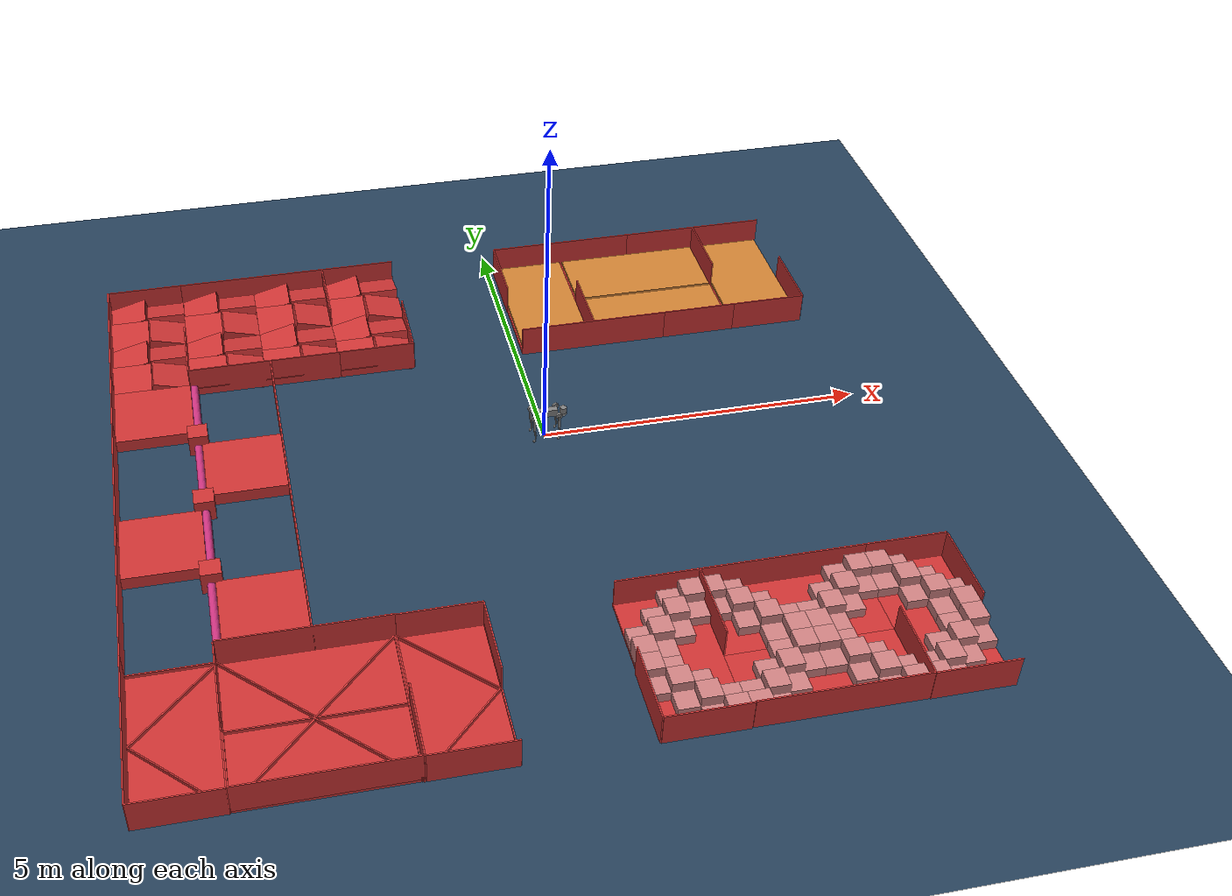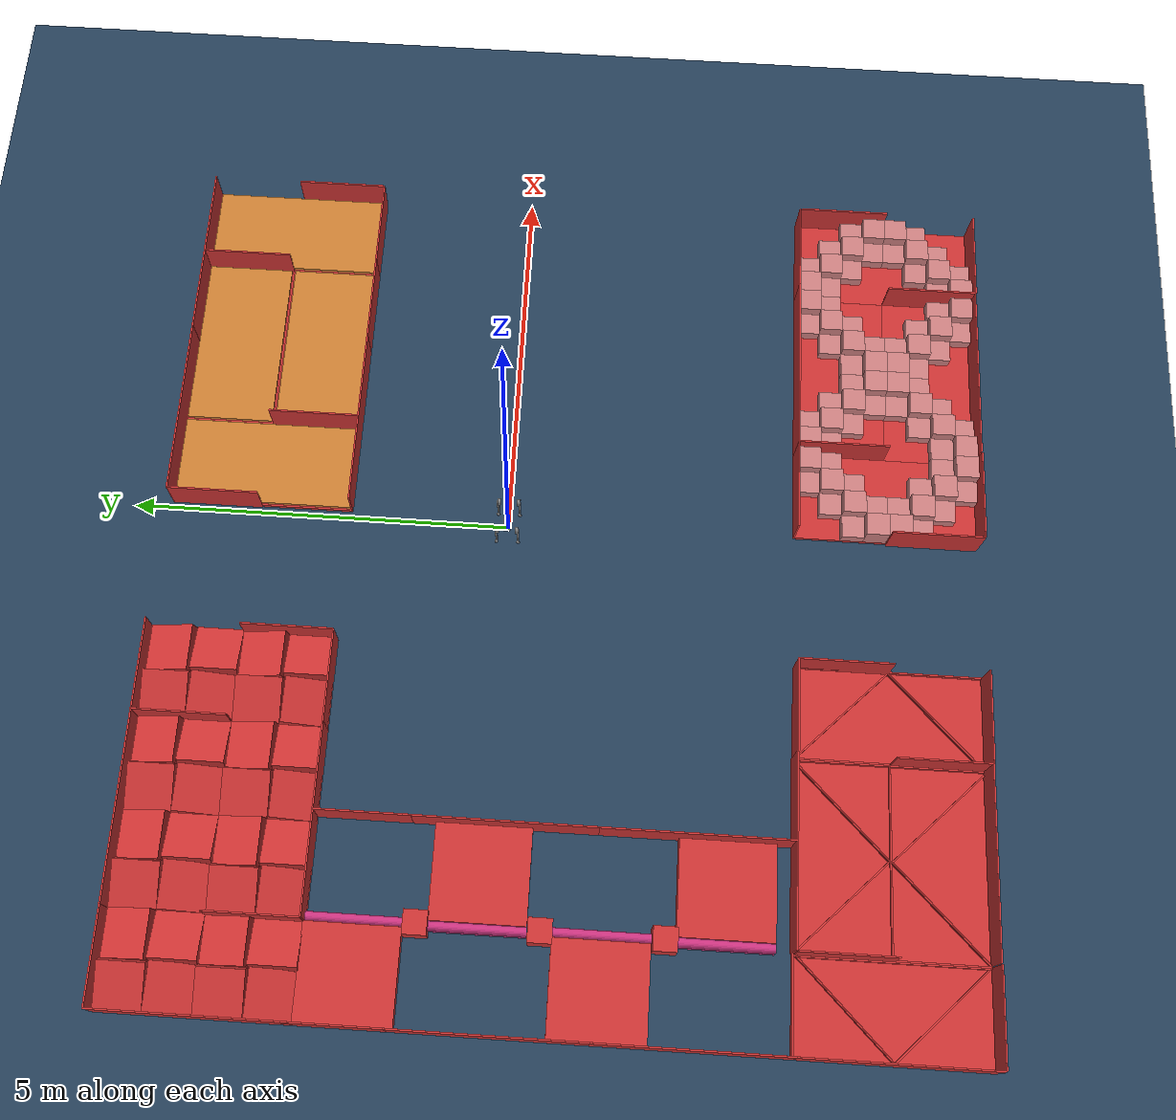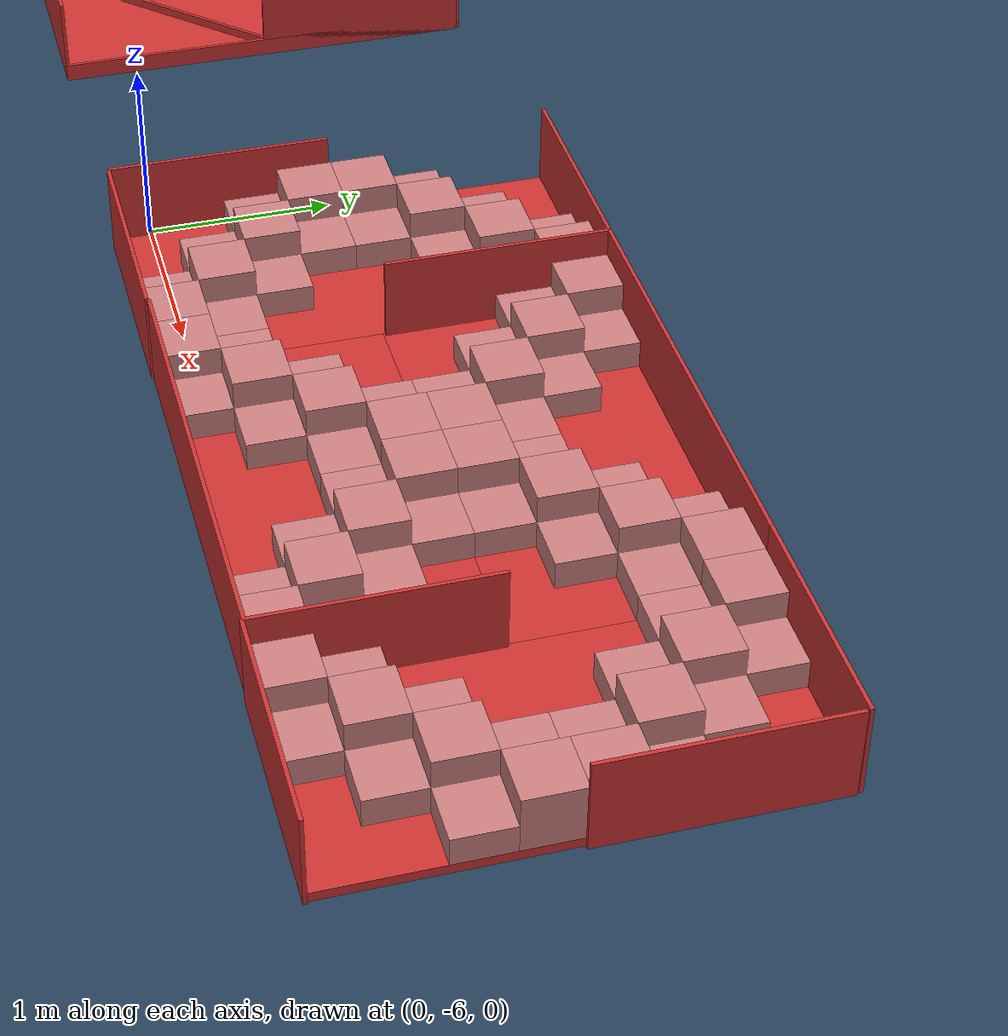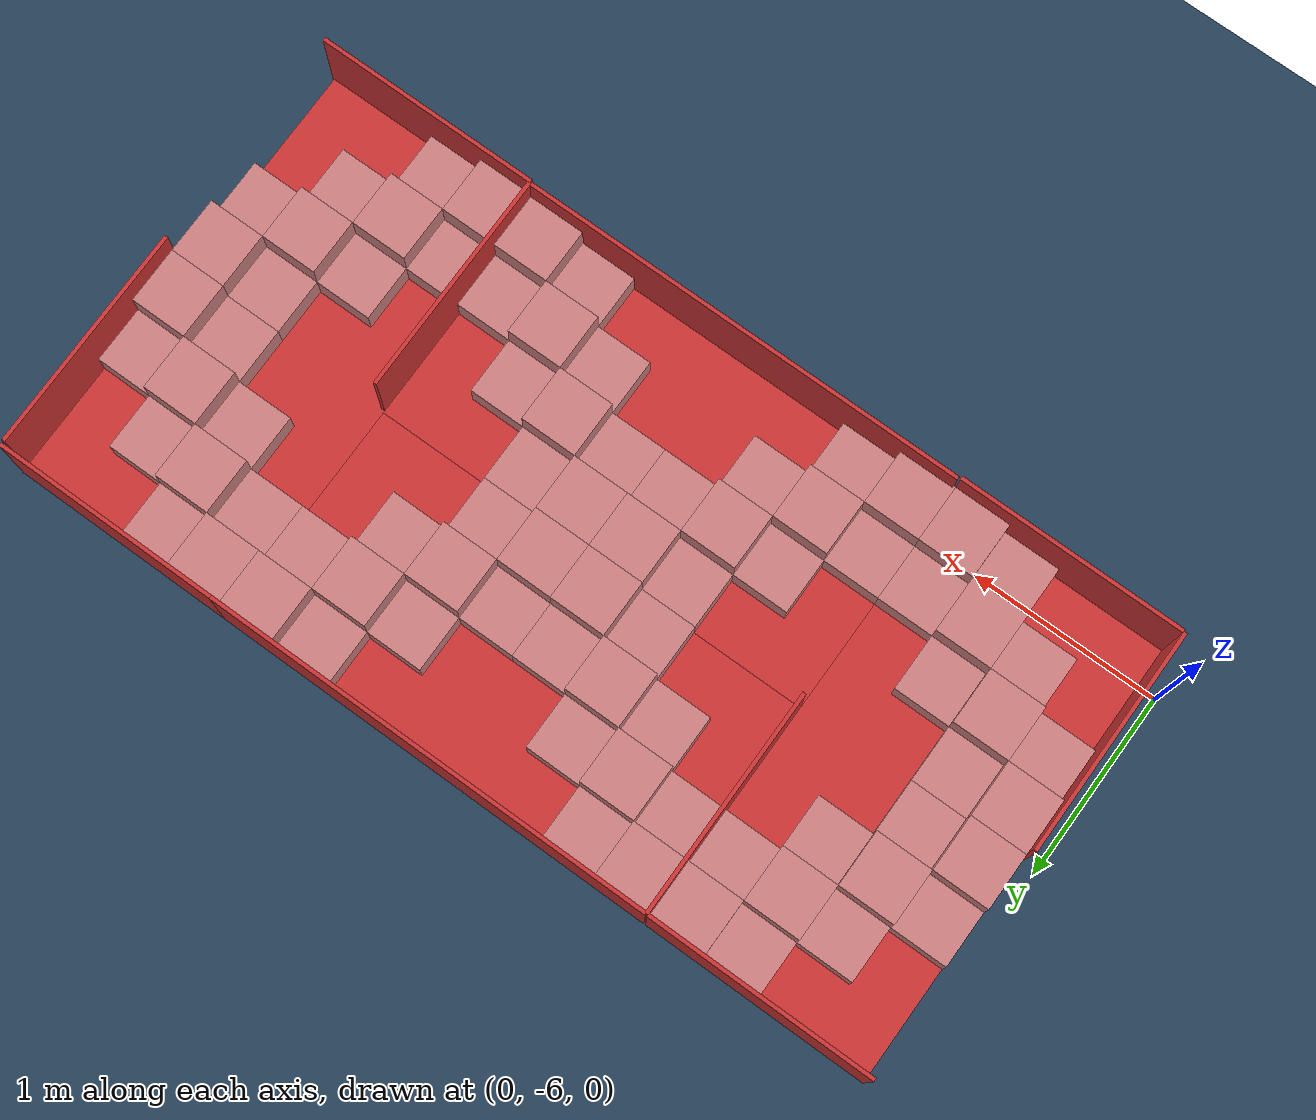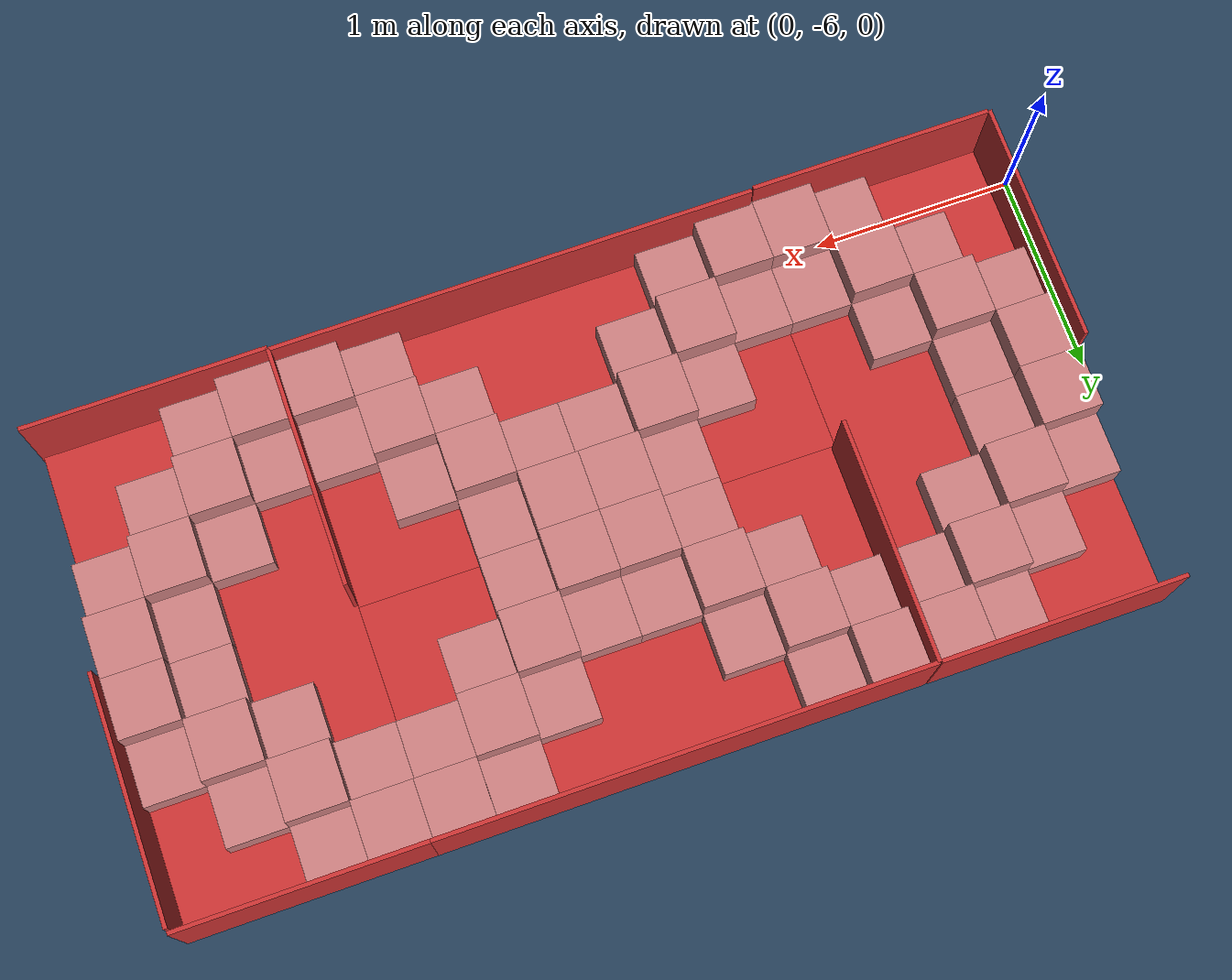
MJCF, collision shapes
<mujoco model="go2 scene">
  <include file="go2.xml" />
  <statistic center="0 0 0.1" extent="0.8" />

  <visual>
    <headlight diffuse="0.6 0.6 0.6" ambient="0.3 0.3 0.3" specular="0 0 0" />
    <rgba haze="0.15 0.25 0.35 1" />
    <global azimuth="-130" elevation="-20" />
    <map znear="0.01" zfar="100"/>
  </visual>

  <asset>
    <texture type="skybox" builtin="gradient" rgb1="0.3 0.5 0.7" rgb2="0 0 0" width="512" height="3072" />
    <texture type="2d" name="groundplane" builtin="checker" mark="edge" rgb1="0.2 0.3 0.4" rgb2="0.1 0.2 0.3" markrgb="0.8 0.8 0.8" width="300" height="300" />
    <material name="groundplane" texture="groundplane" texuniform="true" texrepeat="5 5" reflectance="0.2" />
  <hfield name="perlin_hfield" size="1.0 0.75 0.2 0.2" file="../height_field.png" /><hfield name="image_hfield" size="1.0 1.0 0.02 0.1" file="../unitree_hfield.png" /></asset>

  <worldbody>
    <light pos="0 0 1.5" dir="0 0 -1" directional="true" />
    <geom name="floor" pos="0 0.0 0.001" size="0 0 0.05" type="plane" material="groundplane" />
    <geom name="phs_Cube" type="box" size="0.15 0.15 0.075" pos="4.75 -4.55 0.125" quat="1.0 0.0 0.0 0.0" rgba="0.8 0.5 0.5 1" solref="0.02 1" solimp="0.8 0.05 0.1"/>
    <geom name="phs_Cube2" type="box" size="1.2 0.6 0.025" pos="4.3 -5.0 0.025" quat="0.707107 0.0 0.0 -0.707107" rgba="0.8 0.2 0.2 1" solref="0.02 1" solimp="0.8 0.05 0.1" friction="0.8 0.2 0.05"/>
    <geom name="phs_Cube3" type="box" size="1.2 0.6 0.025" pos="2.5 -4.4 0.025" quat="0.0 0.0 0.0 -1.0" rgba="0.8 0.2 0.2 1" solref="0.02 1" solimp="0.8 0.05 0.1" friction="0.8 0.2 0.05"/>
    <geom name="phs_Cube4" type="box" size="1.2 0.6 0.025" pos="2.5 -5.6 0.025" quat="0.0 0.0 0.0 -1.0" rgba="0.8 0.2 0.2 1" solref="0.02 1" solimp="0.8 0.05 0.1" friction="0.8 0.2 0.05"/>
    <geom name="phs_Cube5" type="box" size="1.2 0.6 0.025" pos="0.7 -5.0 0.025" quat="0.707107 0.0 0.0 -0.707107" rgba="0.8 0.2 0.2 1" solref="0.02 1" solimp="0.8 0.05 0.1" friction="0.8 0.2 0.05"/>
    <geom name="phs_Cube6" type="box" size="1.2 0.6 0.025" pos="-2.3 -5.0 0.025" quat="0.707107 0.0 0.0 -0.707107" rgba="0.8 0.2 0.2 1" solref="0.02 1" solimp="0.8 0.05 0.1" friction="0.8 0.2 0.05"/>
    <geom name="phs_Cube7" type="box" size="1.2 0.6 0.025" pos="-4.1 -4.4 0.025" quat="0.0 0.0 0.0 -1.0" rgba="0.8 0.2 0.2 1" solref="0.02 1" solimp="0.8 0.05 0.1" friction="0.8 0.2 0.05"/>
    <geom name="phs_Cube8" type="box" size="1.2 0.6 0.025" pos="-4.1 -5.6 0.025" quat="0.0 0.0 0.0 -1.0" rgba="0.8 0.2 0.2 1" solref="0.02 1" solimp="0.8 0.05 0.1" friction="0.8 0.2 0.05"/>
    <geom name="phs_Cube9" type="box" size="1.2 0.6 0.025" pos="-5.9 -5.0 0.025" quat="0.707107 0.0 0.0 -0.707107" rgba="0.8 0.2 0.2 1" solref="0.02 1" solimp="0.8 0.05 0.1" friction="0.8 0.2 0.05"/>
    <geom name="phs_Cube10" type="box" size="1.2 0.6 0.025" pos="-2.3 3.3 0.025" quat="0.707107 0.0 0.0 -0.707107" rgba="0.8 0.2 0.2 1" solref="0.02 1" solimp="0.8 0.05 0.1" friction="0.8 0.2 0.05"/>
    <geom name="phs_Cube11" type="box" size="1.2 0.6 0.025" pos="-4.1 3.9 0.025" quat="0.0 0.0 0.0 -1.0" rgba="0.8 0.2 0.2 1" solref="0.02 1" solimp="0.8 0.05 0.1" friction="0.8 0.2 0.05"/>
    <geom name="phs_Cube12" type="box" size="1.2 0.6 0.025" pos="-4.1 2.7 0.025" quat="0.0 0.0 0.0 -1.0" rgba="0.8 0.2 0.2 1" solref="0.02 1" solimp="0.8 0.05 0.1" friction="0.8 0.2 0.05"/>
    <geom name="phs_Cube13" type="box" size="1.2 0.6 0.025" pos="-5.9 3.3 0.025" quat="0.707107 0.0 0.0 -0.707107" rgba="0.8 0.2 0.2 1" solref="0.02 1" solimp="0.8 0.05 0.1" friction="0.8 0.2 0.05"/>
    <geom name="phs_Cube14" type="box" size="1.2 0.6 0.025" pos="4.3 3.3 0.025" quat="0.707107 0.0 0.0 -0.707107" rgba="0.8 0.2 0.2 1" solref="0.02 1" solimp="0.8 0.05 0.1" friction="0.8 0.2 0.05"/>
    <geom name="phs_Cube15" type="box" size="1.2 0.6 0.025" pos="2.5 3.9 0.025" quat="0.0 0.0 0.0 -1.0" rgba="0.8 0.2 0.2 1" solref="0.02 1" solimp="0.8 0.05 0.1" friction="0.8 0.2 0.05"/>
    <geom name="phs_Cube16" type="box" size="1.2 0.6 0.025" pos="2.5 2.7 0.025" quat="0.0 0.0 0.0 -1.0" rgba="0.8 0.2 0.2 1" solref="0.02 1" solimp="0.8 0.05 0.1" friction="0.8 0.2 0.05"/>
    <geom name="phs_Cube17" type="box" size="1.2 0.6 0.025" pos="0.7 3.3 0.025" quat="0.707107 0.0 0.0 -0.707107" rgba="0.8 0.2 0.2 1" solref="0.02 1" solimp="0.8 0.05 0.1" friction="0.8 0.2 0.05"/>
    <geom name="phs_Cube18" type="box" size="0.15 0.15 0.15" pos="4.75 -4.85 0.2" quat="1.0 0.0 0.0 0.0" rgba="0.8 0.5 0.5 1" solref="0.02 1" solimp="0.8 0.05 0.1" friction="0.8 0.2 0.05"/>
    <geom name="phs_Cube19" type="box" size="0.15 0.15 0.15" pos="4.75 -5.15 0.2" quat="1.0 0.0 0.0 0.0" rgba="0.8 0.5 0.5 1" solref="0.02 1" solimp="0.8 0.05 0.1" friction="0.8 0.2 0.05"/>
    <geom name="phs_Cube20" type="box" size="0.15 0.15 0.15" pos="4.45 -5.45 0.2" quat="1.0 0.0 0.0 0.0" rgba="0.8 0.5 0.5 1" solref="0.02 1" solimp="0.8 0.05 0.1" friction="0.8 0.2 0.05"/>
    <geom name="phs_Cube21" type="box" size="0.15 0.15 0.15" pos="4.15 -5.75 0.2" quat="1.0 0.0 0.0 0.0" rgba="0.8 0.5 0.5 1" solref="0.02 1" solimp="0.8 0.05 0.1" friction="0.8 0.2 0.05"/>
    <geom name="phs_Cube22" type="box" size="0.15 0.15 0.15" pos="3.85 -6.05 0.2" quat="1.0 0.0 0.0 0.0" rgba="0.8 0.5 0.5 1" solref="0.02 1" solimp="0.8 0.05 0.1" friction="0.8 0.2 0.05"/>
    <geom name="phs_Cube23" type="box" size="0.15 0.15 0.15" pos="3.85 -3.95 0.2" quat="1.0 0.0 0.0 0.0" rgba="0.8 0.5 0.5 1" solref="0.02 1" solimp="0.8 0.05 0.1" friction="0.8 0.2 0.05"/>
    <geom name="phs_Cube24" type="box" size="0.15 0.15 0.15" pos="4.15 -4.25 0.2" quat="1.0 0.0 0.0 0.0" rgba="0.8 0.5 0.5 1" solref="0.02 1" solimp="0.8 0.05 0.1" friction="0.8 0.2 0.05"/>
    <geom name="phs_Cube25" type="box" size="0.15 0.15 0.15" pos="4.45 -4.55 0.2" quat="1.0 0.0 0.0 0.0" rgba="0.8 0.5 0.5 1" solref="0.02 1" solimp="0.8 0.05 0.1" friction="0.8 0.2 0.05"/>
    <geom name="phs_Cube26" type="box" size="0.15 0.15 0.075" pos="4.45 -4.25 0.125" quat="1.0 0.0 0.0 0.0" rgba="0.8 0.5 0.5 1" solref="0.02 1" solimp="0.8 0.05 0.1" friction="0.8 0.2 0.05"/>
    <geom name="phs_Cube27" type="box" size="0.15 0.15 0.075" pos="4.15 -3.95 0.125" quat="1.0 0.0 0.0 0.0" rgba="0.8 0.5 0.5 1" solref="0.02 1" solimp="0.8 0.05 0.1" friction="0.8 0.2 0.05"/>
    <geom name="phs_Cube28" type="box" size="0.15 0.15 0.075" pos="4.15 -4.55 0.125" quat="1.0 0.0 0.0 0.0" rgba="0.8 0.5 0.5 1" solref="0.02 1" solimp="0.8 0.05 0.1" friction="0.8 0.2 0.05"/>
    <geom name="phs_Cube29" type="box" size="0.15 0.15 0.075" pos="3.85 -4.25 0.125" quat="1.0 0.0 0.0 0.0" rgba="0.8 0.5 0.5 1" solref="0.02 1" solimp="0.8 0.05 0.1" friction="0.8 0.2 0.05"/>
    <geom name="phs_Cube30" type="box" size="0.15 0.15 0.075" pos="4.45 -4.85 0.125" quat="1.0 0.0 0.0 0.0" rgba="0.8 0.5 0.5 1" solref="0.02 1" solimp="0.8 0.05 0.1" friction="0.8 0.2 0.05"/>
    <geom name="phs_Cube31" type="box" size="0.15 0.15 0.075" pos="4.45 -5.15 0.125" quat="1.0 0.0 0.0 0.0" rgba="0.8 0.5 0.5 1" solref="0.02 1" solimp="0.8 0.05 0.1" friction="0.8 0.2 0.05"/>
    <geom name="phs_Cube32" type="box" size="0.15 0.15 0.075" pos="4.45 -5.75 0.125" quat="1.0 0.0 0.0 0.0" rgba="0.8 0.5 0.5 1" solref="0.02 1" solimp="0.8 0.05 0.1" friction="0.8 0.2 0.05"/>
    <geom name="phs_Cube33" type="box" size="0.15 0.15 0.075" pos="4.75 -5.45 0.125" quat="1.0 0.0 0.0 0.0" rgba="0.8 0.5 0.5 1" solref="0.02 1" solimp="0.8 0.05 0.1" friction="0.8 0.2 0.05"/>
    <geom name="phs_Cube34" type="box" size="0.15 0.15 0.075" pos="4.15 -5.45 0.125" quat="1.0 0.0 0.0 0.0" rgba="0.8 0.5 0.5 1" solref="0.02 1" solimp="0.8 0.05 0.1" friction="0.8 0.2 0.05"/>
    <geom name="phs_Cube35" type="box" size="0.15 0.15 0.075" pos="4.15 -6.05 0.125" quat="1.0 0.0 0.0 0.0" rgba="0.8 0.5 0.5 1" solref="0.02 1" solimp="0.8 0.05 0.1" friction="0.8 0.2 0.05"/>
    <geom name="phs_Cube36" type="box" size="0.15 0.15 0.075" pos="3.85 -5.75 0.125" quat="1.0 0.0 0.0 0.0" rgba="0.8 0.5 0.5 1" solref="0.02 1" solimp="0.8 0.05 0.1" friction="0.8 0.2 0.05"/>
    <geom name="phs_Cube37" type="box" size="0.15 0.15 0.075" pos="0.25 -5.45 0.125" quat="0.0 0.0 0.0 -1.0" rgba="0.8 0.5 0.5 1" solref="0.02 1" solimp="0.8 0.05 0.1" friction="0.8 0.2 0.05"/>
    <geom name="phs_Cube38" type="box" size="0.15 0.15 0.15" pos="0.25 -5.15 0.2" quat="0.0 0.0 0.0 -1.0" rgba="0.8 0.5 0.5 1" solref="0.02 1" solimp="0.8 0.05 0.1" friction="0.8 0.2 0.05"/>
    <geom name="phs_Cube39" type="box" size="0.15 0.15 0.15" pos="0.25 -4.85 0.2" quat="0.0 0.0 0.0 -1.0" rgba="0.8 0.5 0.5 1" solref="0.02 1" solimp="0.8 0.05 0.1" friction="0.8 0.2 0.05"/>
    <geom name="phs_Cube40" type="box" size="0.15 0.15 0.15" pos="0.55 -4.55 0.2" quat="0.0 0.0 0.0 -1.0" rgba="0.8 0.5 0.5 1" solref="0.02 1" solimp="0.8 0.05 0.1" friction="0.8 0.2 0.05"/>
    <geom name="phs_Cube41" type="box" size="0.15 0.15 0.15" pos="0.85 -4.25 0.2" quat="0.0 0.0 0.0 -1.0" rgba="0.8 0.5 0.5 1" solref="0.02 1" solimp="0.8 0.05 0.1" friction="0.8 0.2 0.05"/>
    <geom name="phs_Cube42" type="box" size="0.15 0.15 0.15" pos="1.15 -3.95 0.2" quat="0.0 0.0 0.0 -1.0" rgba="0.8 0.5 0.5 1" solref="0.02 1" solimp="0.8 0.05 0.1" friction="0.8 0.2 0.05"/>
    <geom name="phs_Cube43" type="box" size="0.15 0.15 0.15" pos="1.15 -6.05 0.2" quat="0.0 0.0 0.0 -1.0" rgba="0.8 0.5 0.5 1" solref="0.02 1" solimp="0.8 0.05 0.1" friction="0.8 0.2 0.05"/>
    <geom name="phs_Cube44" type="box" size="0.15 0.15 0.15" pos="0.85 -5.75 0.2" quat="0.0 0.0 0.0 -1.0" rgba="0.8 0.5 0.5 1" solref="0.02 1" solimp="0.8 0.05 0.1" friction="0.8 0.2 0.05"/>
    <geom name="phs_Cube45" type="box" size="0.15 0.15 0.15" pos="0.55 -5.45 0.2" quat="0.0 0.0 0.0 -1.0" rgba="0.8 0.5 0.5 1" solref="0.02 1" solimp="0.8 0.05 0.1" friction="0.8 0.2 0.05"/>
    <geom name="phs_Cube46" type="box" size="0.15 0.15 0.075" pos="0.55 -5.75 0.125" quat="0.0 0.0 0.0 -1.0" rgba="0.8 0.5 0.5 1" solref="0.02 1" solimp="0.8 0.05 0.1" friction="0.8 0.2 0.05"/>
    <geom name="phs_Cube47" type="box" size="0.15 0.15 0.075" pos="0.85 -6.05 0.125" quat="0.0 0.0 0.0 -1.0" rgba="0.8 0.5 0.5 1" solref="0.02 1" solimp="0.8 0.05 0.1" friction="0.8 0.2 0.05"/>
    <geom name="phs_Cube48" type="box" size="0.15 0.15 0.075" pos="0.85 -5.45 0.125" quat="0.0 0.0 0.0 -1.0" rgba="0.8 0.5 0.5 1" solref="0.02 1" solimp="0.8 0.05 0.1" friction="0.8 0.2 0.05"/>
    <geom name="phs_Cube49" type="box" size="0.15 0.15 0.075" pos="1.15 -5.75 0.125" quat="0.0 0.0 0.0 -1.0" rgba="0.8 0.5 0.5 1" solref="0.02 1" solimp="0.8 0.05 0.1" friction="0.8 0.2 0.05"/>
    <geom name="phs_Cube50" type="box" size="0.15 0.15 0.075" pos="0.55 -5.15 0.125" quat="0.0 0.0 0.0 -1.0" rgba="0.8 0.5 0.5 1" solref="0.02 1" solimp="0.8 0.05 0.1" friction="0.8 0.2 0.05"/>
    <geom name="phs_Cube51" type="box" size="0.15 0.15 0.075" pos="0.55 -4.85 0.125" quat="0.0 0.0 0.0 -1.0" rgba="0.8 0.5 0.5 1" solref="0.02 1" solimp="0.8 0.05 0.1" friction="0.8 0.2 0.05"/>
    <geom name="phs_Cube52" type="box" size="0.15 0.15 0.075" pos="0.55 -4.25 0.125" quat="0.0 0.0 0.0 -1.0" rgba="0.8 0.5 0.5 1" solref="0.02 1" solimp="0.8 0.05 0.1" friction="0.8 0.2 0.05"/>
    <geom name="phs_Cube53" type="box" size="0.15 0.15 0.075" pos="0.25 -4.55 0.125" quat="0.0 0.0 0.0 -1.0" rgba="0.8 0.5 0.5 1" solref="0.02 1" solimp="0.8 0.05 0.1" friction="0.8 0.2 0.05"/>
    <geom name="phs_Cube54" type="box" size="0.15 0.15 0.075" pos="0.85 -4.55 0.125" quat="0.0 0.0 0.0 -1.0" rgba="0.8 0.5 0.5 1" solref="0.02 1" solimp="0.8 0.05 0.1" friction="0.8 0.2 0.05"/>
    <geom name="phs_Cube55" type="box" size="0.15 0.15 0.075" pos="0.85 -3.95 0.125" quat="0.0 0.0 0.0 -1.0" rgba="0.8 0.5 0.5 1" solref="0.02 1" solimp="0.8 0.05 0.1" friction="0.8 0.2 0.05"/>
    <geom name="phs_Cube56" type="box" size="0.15 0.15 0.075" pos="1.15 -4.25 0.125" quat="0.0 0.0 0.0 -1.0" rgba="0.8 0.5 0.5 1" solref="0.02 1" solimp="0.8 0.05 0.1" friction="0.8 0.2 0.05"/>
    <geom name="phs_Cube57" type="box" size="0.15 0.15 0.075" pos="2.95 -4.85 0.125" quat="0.707107 0.0 0.0 -0.707107" rgba="0.8 0.5 0.5 1" solref="0.02 1" solimp="0.8 0.05 0.1" friction="0.8 0.2 0.05"/>
    <geom name="phs_Cube58" type="box" size="0.15 0.15 0.15" pos="2.65 -4.85 0.2" quat="0.707107 0.0 0.0 -0.707107" rgba="0.8 0.5 0.5 1" solref="0.02 1" solimp="0.8 0.05 0.1" friction="0.8 0.2 0.05"/>
    <geom name="phs_Cube59" type="box" size="0.15 0.15 0.15" pos="2.35 -4.85 0.2" quat="0.707107 0.0 0.0 -0.707107" rgba="0.8 0.5 0.5 1" solref="0.02 1" solimp="0.8 0.05 0.1" friction="0.8 0.2 0.05"/>
    <geom name="phs_Cube60" type="box" size="0.15 0.15 0.15" pos="2.05 -4.55 0.2" quat="0.707107 0.0 0.0 -0.707107" rgba="0.8 0.5 0.5 1" solref="0.02 1" solimp="0.8 0.05 0.1" friction="0.8 0.2 0.05"/>
    <geom name="phs_Cube61" type="box" size="0.15 0.15 0.15" pos="1.75 -4.25 0.2" quat="0.707107 0.0 0.0 -0.707107" rgba="0.8 0.5 0.5 1" solref="0.02 1" solimp="0.8 0.05 0.1" friction="0.8 0.2 0.05"/>
    <geom name="phs_Cube62" type="box" size="0.15 0.15 0.15" pos="1.45 -3.95 0.2" quat="0.707107 0.0 0.0 -0.707107" rgba="0.8 0.5 0.5 1" solref="0.02 1" solimp="0.8 0.05 0.1" friction="0.8 0.2 0.05"/>
    <geom name="phs_Cube63" type="box" size="0.15 0.15 0.15" pos="3.55 -3.95 0.2" quat="0.707107 0.0 0.0 -0.707107" rgba="0.8 0.5 0.5 1" solref="0.02 1" solimp="0.8 0.05 0.1" friction="0.8 0.2 0.05"/>
    <geom name="phs_Cube64" type="box" size="0.15 0.15 0.15" pos="3.25 -4.25 0.2" quat="0.707107 0.0 0.0 -0.707107" rgba="0.8 0.5 0.5 1" solref="0.02 1" solimp="0.8 0.05 0.1" friction="0.8 0.2 0.05"/>
    <geom name="phs_Cube65" type="box" size="0.15 0.15 0.15" pos="2.95 -4.55 0.2" quat="0.707107 0.0 0.0 -0.707107" rgba="0.8 0.5 0.5 1" solref="0.02 1" solimp="0.8 0.05 0.1" friction="0.8 0.2 0.05"/>
    <geom name="phs_Cube66" type="box" size="0.15 0.15 0.075" pos="3.25 -4.55 0.125" quat="0.707107 0.0 0.0 -0.707107" rgba="0.8 0.5 0.5 1" solref="0.02 1" solimp="0.8 0.05 0.1" friction="0.8 0.2 0.05"/>
    <geom name="phs_Cube67" type="box" size="0.15 0.15 0.075" pos="3.55 -4.25 0.125" quat="0.707107 0.0 0.0 -0.707107" rgba="0.8 0.5 0.5 1" solref="0.02 1" solimp="0.8 0.05 0.1" friction="0.8 0.2 0.05"/>
    <geom name="phs_Cube68" type="box" size="0.15 0.15 0.075" pos="2.95 -4.25 0.125" quat="0.707107 0.0 0.0 -0.707107" rgba="0.8 0.5 0.5 1" solref="0.02 1" solimp="0.8 0.05 0.1" friction="0.8 0.2 0.05"/>
    <geom name="phs_Cube69" type="box" size="0.15 0.15 0.075" pos="3.25 -3.95 0.125" quat="0.707107 0.0 0.0 -0.707107" rgba="0.8 0.5 0.5 1" solref="0.02 1" solimp="0.8 0.05 0.1" friction="0.8 0.2 0.05"/>
    <geom name="phs_Cube70" type="box" size="0.15 0.15 0.075" pos="2.65 -4.55 0.125" quat="0.707107 0.0 0.0 -0.707107" rgba="0.8 0.5 0.5 1" solref="0.02 1" solimp="0.8 0.05 0.1" friction="0.8 0.2 0.05"/>
    <geom name="phs_Cube71" type="box" size="0.15 0.15 0.075" pos="2.35 -4.55 0.125" quat="0.707107 0.0 0.0 -0.707107" rgba="0.8 0.5 0.5 1" solref="0.02 1" solimp="0.8 0.05 0.1" friction="0.8 0.2 0.05"/>
    <geom name="phs_Cube72" type="box" size="0.15 0.15 0.075" pos="1.75 -4.55 0.125" quat="0.707107 0.0 0.0 -0.707107" rgba="0.8 0.5 0.5 1" solref="0.02 1" solimp="0.8 0.05 0.1" friction="0.8 0.2 0.05"/>
    <geom name="phs_Cube73" type="box" size="0.15 0.15 0.075" pos="2.05 -4.85 0.125" quat="0.707107 0.0 0.0 -0.707107" rgba="0.8 0.5 0.5 1" solref="0.02 1" solimp="0.8 0.05 0.1" friction="0.8 0.2 0.05"/>
    <geom name="phs_Cube74" type="box" size="0.15 0.15 0.075" pos="2.05 -4.25 0.125" quat="0.707107 0.0 0.0 -0.707107" rgba="0.8 0.5 0.5 1" solref="0.02 1" solimp="0.8 0.05 0.1" friction="0.8 0.2 0.05"/>
    <geom name="phs_Cube75" type="box" size="0.15 0.15 0.075" pos="1.45 -4.25 0.125" quat="0.707107 0.0 0.0 -0.707107" rgba="0.8 0.5 0.5 1" solref="0.02 1" solimp="0.8 0.05 0.1" friction="0.8 0.2 0.05"/>
    <geom name="phs_Cube76" type="box" size="0.15 0.15 0.075" pos="1.75 -3.95 0.125" quat="0.707107 0.0 0.0 -0.707107" rgba="0.8 0.5 0.5 1" solref="0.02 1" solimp="0.8 0.05 0.1" friction="0.8 0.2 0.05"/>
    <geom name="phs_Cube77" type="box" size="0.15 0.15 0.075" pos="2.05 -5.15 0.125" quat="0.707107 0.0 0.0 0.707107" rgba="0.8 0.5 0.5 1" solref="0.02 1" solimp="0.8 0.05 0.1" friction="0.8 0.2 0.05"/>
    <geom name="phs_Cube78" type="box" size="0.15 0.15 0.15" pos="2.35 -5.15 0.2" quat="0.707107 0.0 0.0 0.707107" rgba="0.8 0.5 0.5 1" solref="0.02 1" solimp="0.8 0.05 0.1" friction="0.8 0.2 0.05"/>
    <geom name="phs_Cube79" type="box" size="0.15 0.15 0.15" pos="2.65 -5.15 0.2" quat="0.707107 0.0 0.0 0.707107" rgba="0.8 0.5 0.5 1" solref="0.02 1" solimp="0.8 0.05 0.1" friction="0.8 0.2 0.05"/>
    <geom name="phs_Cube80" type="box" size="0.15 0.15 0.15" pos="2.95 -5.45 0.2" quat="0.707107 0.0 0.0 0.707107" rgba="0.8 0.5 0.5 1" solref="0.02 1" solimp="0.8 0.05 0.1" friction="0.8 0.2 0.05"/>
    <geom name="phs_Cube81" type="box" size="0.15 0.15 0.15" pos="3.25 -5.75 0.2" quat="0.707107 0.0 0.0 0.707107" rgba="0.8 0.5 0.5 1" solref="0.02 1" solimp="0.8 0.05 0.1" friction="0.8 0.2 0.05"/>
    <geom name="phs_Cube82" type="box" size="0.15 0.15 0.15" pos="3.55 -6.05 0.2" quat="0.707107 0.0 0.0 0.707107" rgba="0.8 0.5 0.5 1" solref="0.02 1" solimp="0.8 0.05 0.1" friction="0.8 0.2 0.05"/>
    <geom name="phs_Cube83" type="box" size="0.15 0.15 0.15" pos="1.45 -6.05 0.2" quat="0.707107 0.0 0.0 0.707107" rgba="0.8 0.5 0.5 1" solref="0.02 1" solimp="0.8 0.05 0.1" friction="0.8 0.2 0.05"/>
    <geom name="phs_Cube84" type="box" size="0.15 0.15 0.15" pos="1.75 -5.75 0.2" quat="0.707107 0.0 0.0 0.707107" rgba="0.8 0.5 0.5 1" solref="0.02 1" solimp="0.8 0.05 0.1" friction="0.8 0.2 0.05"/>
    <geom name="phs_Cube85" type="box" size="0.15 0.15 0.15" pos="2.05 -5.45 0.2" quat="0.707107 0.0 0.0 0.707107" rgba="0.8 0.5 0.5 1" solref="0.02 1" solimp="0.8 0.05 0.1" friction="0.8 0.2 0.05"/>
    <geom name="phs_Cube86" type="box" size="0.15 0.15 0.075" pos="1.75 -5.45 0.125" quat="0.707107 0.0 0.0 0.707107" rgba="0.8 0.5 0.5 1" solref="0.02 1" solimp="0.8 0.05 0.1" friction="0.8 0.2 0.05"/>
    <geom name="phs_Cube87" type="box" size="0.15 0.15 0.075" pos="1.45 -5.75 0.125" quat="0.707107 0.0 0.0 0.707107" rgba="0.8 0.5 0.5 1" solref="0.02 1" solimp="0.8 0.05 0.1" friction="0.8 0.2 0.05"/>
    <geom name="phs_Cube88" type="box" size="0.15 0.15 0.075" pos="2.05 -5.75 0.125" quat="0.707107 0.0 0.0 0.707107" rgba="0.8 0.5 0.5 1" solref="0.02 1" solimp="0.8 0.05 0.1" friction="0.8 0.2 0.05"/>
    <geom name="phs_Cube89" type="box" size="0.15 0.15 0.075" pos="1.75 -6.05 0.125" quat="0.707107 0.0 0.0 0.707107" rgba="0.8 0.5 0.5 1" solref="0.02 1" solimp="0.8 0.05 0.1" friction="0.8 0.2 0.05"/>
    <geom name="phs_Cube90" type="box" size="0.15 0.15 0.075" pos="2.35 -5.45 0.125" quat="0.707107 0.0 0.0 0.707107" rgba="0.8 0.5 0.5 1" solref="0.02 1" solimp="0.8 0.05 0.1" friction="0.8 0.2 0.05"/>
    <geom name="phs_Cube91" type="box" size="0.15 0.15 0.075" pos="2.65 -5.45 0.125" quat="0.707107 0.0 0.0 0.707107" rgba="0.8 0.5 0.5 1" solref="0.02 1" solimp="0.8 0.05 0.1" friction="0.8 0.2 0.05"/>
    <geom name="phs_Cube92" type="box" size="0.15 0.15 0.075" pos="3.25 -5.45 0.125" quat="0.707107 0.0 0.0 0.707107" rgba="0.8 0.5 0.5 1" solref="0.02 1" solimp="0.8 0.05 0.1" friction="0.8 0.2 0.05"/>
    <geom name="phs_Cube93" type="box" size="0.15 0.15 0.075" pos="2.95 -5.15 0.125" quat="0.707107 0.0 0.0 0.707107" rgba="0.8 0.5 0.5 1" solref="0.02 1" solimp="0.8 0.05 0.1" friction="0.8 0.2 0.05"/>
    <geom name="phs_Cube94" type="box" size="0.15 0.15 0.075" pos="2.95 -5.75 0.125" quat="0.707107 0.0 0.0 0.707107" rgba="0.8 0.5 0.5 1" solref="0.02 1" solimp="0.8 0.05 0.1" friction="0.8 0.2 0.05"/>
    <geom name="phs_Cube95" type="box" size="0.15 0.15 0.075" pos="3.55 -5.75 0.125" quat="0.707107 0.0 0.0 0.707107" rgba="0.8 0.5 0.5 1" solref="0.02 1" solimp="0.8 0.05 0.1" friction="0.8 0.2 0.05"/>
    <geom name="phs_Cube96" type="box" size="0.15 0.15 0.075" pos="3.25 -6.05 0.125" quat="0.707107 0.0 0.0 0.707107" rgba="0.8 0.5 0.5 1" solref="0.02 1" solimp="0.8 0.05 0.1" friction="0.8 0.2 0.05"/>
    <geom name="phs_Cube97" type="box" size="0.6 0.01 0.25" pos="4.31 -6.21 0.25" quat="1.0 0.0 0.0 0.0" rgba="0.8 0.2 0.2 1" solref="0.02 1" solimp="0.8 0.05 0.1" friction="0.8 0.2 0.05"/>
    <geom name="phs_Cube98" type="box" size="0.6 0.01 0.25" pos="4.31 -3.79 0.25" quat="1.0 0.0 0.0 0.0" rgba="0.8 0.2 0.2 1" solref="0.02 1" solimp="0.8 0.05 0.1" friction="0.8 0.2 0.05"/>
    <geom name="phs_Cube99" type="box" size="0.6 0.01 0.25" pos="0.7 -6.21 0.25" quat="1.0 0.0 0.0 0.0" rgba="0.8 0.2 0.2 1" solref="0.02 1" solimp="0.8 0.05 0.1" friction="0.8 0.2 0.05"/>
    <geom name="phs_Cube100" type="box" size="0.6 0.01 0.25" pos="0.7 -3.79 0.25" quat="1.0 0.0 0.0 0.0" rgba="0.8 0.2 0.2 1" solref="0.02 1" solimp="0.8 0.05 0.1" friction="0.8 0.2 0.05"/>
    <geom name="phs_Cube101" type="box" size="0.6 0.01 0.25" pos="4.91 -4.41 0.25" quat="0.707107 0.0 0.0 -0.707107" rgba="0.8 0.2 0.2 1" solref="0.02 1" solimp="0.8 0.05 0.1" friction="0.8 0.2 0.05"/>
    <geom name="phs_Cube102" type="box" size="0.6 0.01 0.25" pos="1.31 -4.39 0.25" quat="0.707107 0.0 0.0 -0.707107" rgba="0.8 0.2 0.2 1" solref="0.02 1" solimp="0.8 0.05 0.1" friction="0.8 0.2 0.05"/>
    <geom name="phs_Cube103" type="box" size="0.6 0.01 0.25" pos="0.09 -5.61 0.25" quat="0.707107 0.0 0.0 -0.707107" rgba="0.8 0.2 0.2 1" solref="0.02 1" solimp="0.8 0.05 0.1" friction="0.8 0.2 0.05"/>
    <geom name="phs_Cube104" type="box" size="0.6 0.01 0.25" pos="3.71 -5.61 0.25" quat="0.707107 0.0 0.0 -0.707107" rgba="0.8 0.2 0.2 1" solref="0.02 1" solimp="0.8 0.05 0.1" friction="0.8 0.2 0.05"/>
    <geom name="phs_Cube105" type="box" size="1.2 0.01 0.25" pos="2.51 -3.79 0.25" quat="1.0 0.0 0.0 0.0" rgba="0.8 0.2 0.2 1" solref="0.02 1" solimp="0.8 0.05 0.1" friction="0.8 0.2 0.05"/>
    <geom name="phs_Cube106" type="box" size="1.2 0.01 0.25" pos="2.51 -6.2 0.25" quat="1.0 0.0 0.0 0.0" rgba="0.8 0.2 0.2 1" solref="0.02 1" solimp="0.8 0.05 0.1" friction="0.8 0.2 0.05"/>
    <geom name="phs_Cube107" type="box" size="1.2 0.01 0.25" pos="-4.09 -6.19 0.25" quat="1.0 0.0 0.0 0.0" rgba="0.8 0.2 0.2 1" solref="0.02 1" solimp="0.8 0.05 0.1" friction="0.8 0.2 0.05"/>
    <geom name="phs_Cube108" type="box" size="1.2 0.01 0.25" pos="-4.09 -3.79 0.25" quat="1.0 0.0 0.0 0.0" rgba="0.8 0.2 0.2 1" solref="0.02 1" solimp="0.8 0.05 0.1" friction="0.8 0.2 0.05"/>
    <geom name="phs_Cube109" type="box" size="1.2 0.01 0.25" pos="-6.5 -5.0 0.25" quat="0.707107 0.0 0.0 0.707107" rgba="0.8 0.2 0.2 1" solref="0.02 1" solimp="0.8 0.05 0.1" friction="0.8 0.2 0.05"/>
    <geom name="phs_Cube110" type="box" size="1.2 0.01 0.25" pos="-6.5 -2.6 0.25" quat="0.707107 0.0 0.0 0.707107" rgba="0.8 0.2 0.2 1" solref="0.02 1" solimp="0.8 0.05 0.1" friction="0.8 0.2 0.05"/>
    <geom name="phs_Cube111" type="box" size="1.2 0.01 0.25" pos="-6.5 -0.2 0.25" quat="0.707107 0.0 0.0 0.707107" rgba="0.8 0.2 0.2 1" solref="0.02 1" solimp="0.8 0.05 0.1" friction="0.8 0.2 0.05"/>
    <geom name="phs_Cube112" type="box" size="1.2 0.01 0.25" pos="-4.0 -2.6 0.25" quat="0.707107 0.0 0.0 0.707107" rgba="0.8 0.2 0.2 1" solref="0.02 1" solimp="0.8 0.05 0.1" friction="0.8 0.2 0.05"/>
    <geom name="phs_Cube113" type="box" size="1.2 0.01 0.25" pos="-4.0 -0.2 0.25" quat="0.707107 0.0 0.0 0.707107" rgba="0.8 0.2 0.2 1" solref="0.02 1" solimp="0.8 0.05 0.1" friction="0.8 0.2 0.05"/>
    <geom name="phs_Cube114" type="box" size="0.6 0.01 0.25" pos="-1.7 -4.41 0.25" quat="0.707107 0.0 0.0 -0.707107" rgba="0.8 0.2 0.2 1" solref="0.02 1" solimp="0.8 0.05 0.1" friction="0.8 0.2 0.05"/>
    <geom name="phs_Cube115" type="box" size="0.6 0.01 0.25" pos="-5.3 -4.41 0.25" quat="0.707107 0.0 0.0 -0.707107" rgba="0.8 0.2 0.2 1" solref="0.02 1" solimp="0.8 0.05 0.1" friction="0.8 0.2 0.05"/>
    <geom name="phs_Cube116" type="box" size="0.6 0.01 0.25" pos="-2.9 -5.61 0.25" quat="0.707107 0.0 0.0 -0.707107" rgba="0.8 0.2 0.2 1" solref="0.02 1" solimp="0.8 0.05 0.1" friction="0.8 0.2 0.05"/>
    <geom name="phs_Cube117" type="box" size="0.6 0.01 0.25" pos="-2.3 -6.2 0.25" quat="0.0 0.0 0.0 -1.0" rgba="0.8 0.2 0.2 1" solref="0.02 1" solimp="0.8 0.05 0.1" friction="0.8 0.2 0.05"/>
    <geom name="phs_Cube118" type="box" size="0.6 0.01 0.25" pos="-2.3 -3.8 0.25" quat="0.0 0.0 0.0 -1.0" rgba="0.8 0.2 0.2 1" solref="0.02 1" solimp="0.8 0.05 0.1" friction="0.8 0.2 0.05"/>
    <geom name="phs_Cube119" type="box" size="0.6 0.01 0.25" pos="-5.9 -6.2 0.25" quat="0.0 0.0 0.0 -1.0" rgba="0.8 0.2 0.2 1" solref="0.02 1" solimp="0.8 0.05 0.1" friction="0.8 0.2 0.05"/>
    <geom name="phs_Cube120" type="box" size="0.6 0.01 0.25" pos="-6.5 1.59 0.25" quat="0.707107 0.0 0.0 -0.707107" rgba="0.8 0.2 0.2 1" solref="0.02 1" solimp="0.8 0.05 0.1" friction="0.8 0.2 0.05"/>
    <geom name="phs_Cube121" type="box" size="0.6 0.01 0.25" pos="-4.0 1.5 0.25" quat="0.707107 0.0 0.0 -0.707107" rgba="0.8 0.2 0.2 1" solref="0.02 1" solimp="0.8 0.05 0.1" friction="0.8 0.2 0.05"/>
    <geom name="phs_Cube122" type="box" size="0.6 0.01 0.25" pos="-5.3 2.7 0.25" quat="0.707107 0.0 0.0 -0.707107" rgba="0.8 0.2 0.2 1" solref="0.02 1" solimp="0.8 0.05 0.1" friction="0.8 0.2 0.05"/>
    <geom name="phs_Cube123" type="box" size="0.6 0.01 0.25" pos="-1.7 2.7 0.25" quat="0.707107 0.0 0.0 -0.707107" rgba="0.8 0.2 0.2 1" solref="0.02 1" solimp="0.8 0.05 0.1" friction="0.8 0.2 0.05"/>
    <geom name="phs_Cube124" type="box" size="0.6 0.01 0.25" pos="-2.3 2.1 0.25" quat="0.0 0.0 0.0 -1.0" rgba="0.8 0.2 0.2 1" solref="0.02 1" solimp="0.8 0.05 0.1" friction="0.8 0.2 0.05"/>
    <geom name="phs_Cube125" type="box" size="0.6 0.01 0.25" pos="-2.3 4.5 0.25" quat="0.0 0.0 0.0 -1.0" rgba="0.8 0.2 0.2 1" solref="0.02 1" solimp="0.8 0.05 0.1" friction="0.8 0.2 0.05"/>
    <geom name="phs_Cube126" type="box" size="0.6 0.01 0.25" pos="-5.9 4.5 0.25" quat="0.0 0.0 0.0 -1.0" rgba="0.8 0.2 0.2 1" solref="0.02 1" solimp="0.8 0.05 0.1" friction="0.8 0.2 0.05"/>
    <geom name="phs_Cube127" type="box" size="0.6 0.01 0.25" pos="-2.9 3.9 0.25" quat="0.707107 0.0 0.0 -0.707107" rgba="0.8 0.2 0.2 1" solref="0.02 1" solimp="0.8 0.05 0.1" friction="0.8 0.2 0.05"/>
    <geom name="phs_Cube128" type="box" size="1.2 0.01 0.25" pos="-4.1 2.1 0.25" quat="1.0 0.0 0.0 -0.0" rgba="0.8 0.2 0.2 1" solref="0.02 1" solimp="0.8 0.05 0.1" friction="0.8 0.2 0.05"/>
    <geom name="phs_Cube129" type="box" size="1.2 0.01 0.25" pos="-4.1 4.5 0.25" quat="1.0 0.0 0.0 0.0" rgba="0.8 0.2 0.2 1" solref="0.02 1" solimp="0.8 0.05 0.1" friction="0.8 0.2 0.05"/>
    <geom name="phs_Cube130" type="box" size="1.2 0.01 0.25" pos="-6.5 3.3 0.25" quat="0.707107 0.0 0.0 0.707107" rgba="0.8 0.2 0.2 1" solref="0.02 1" solimp="0.8 0.05 0.1" friction="0.8 0.2 0.05"/>
    <geom name="phs_Cube131" type="box" size="0.6 0.01 0.25" pos="4.9 2.7 0.25" quat="0.707107 0.0 0.0 -0.707107" rgba="0.8 0.2 0.2 1" solref="0.02 1" solimp="0.8 0.05 0.1" friction="0.8 0.2 0.05"/>
    <geom name="phs_Cube132" type="box" size="0.6 0.01 0.25" pos="3.7 3.9 0.25" quat="0.707107 0.0 0.0 -0.707107" rgba="0.8 0.2 0.2 1" solref="0.02 1" solimp="0.8 0.05 0.1" friction="0.8 0.2 0.05"/>
    <geom name="phs_Cube133" type="box" size="0.6 0.01 0.25" pos="0.1 3.9 0.25" quat="0.707107 0.0 0.0 -0.707107" rgba="0.8 0.2 0.2 1" solref="0.02 1" solimp="0.8 0.05 0.1" friction="0.8 0.2 0.05"/>
    <geom name="phs_Cube134" type="box" size="0.6 0.01 0.25" pos="1.3 2.7 0.25" quat="0.707107 0.0 0.0 -0.707107" rgba="0.8 0.2 0.2 1" solref="0.02 1" solimp="0.8 0.05 0.1" friction="0.8 0.2 0.05"/>
    <geom name="phs_Cube135" type="box" size="0.6 0.01 0.25" pos="3.1 2.1 0.25" quat="0.0 0.0 0.0 -1.0" rgba="0.8 0.2 0.2 1" solref="0.02 1" solimp="0.8 0.05 0.1" friction="0.8 0.2 0.05"/>
    <geom name="phs_Cube136" type="box" size="1.2 0.01 0.25" pos="1.3 2.1 0.25" quat="1.0 0.0 0.0 0.0" rgba="0.8 0.2 0.2 1" solref="0.02 1" solimp="0.8 0.05 0.1" friction="0.8 0.2 0.05"/>
    <geom name="phs_Cube137" type="box" size="0.6 0.01 0.25" pos="3.1 4.5 0.25" quat="0.0 0.0 0.0 -1.0" rgba="0.8 0.2 0.2 1" solref="0.02 1" solimp="0.8 0.05 0.1" friction="0.8 0.2 0.05"/>
    <geom name="phs_Cube138" type="box" size="1.2 0.01 0.25" pos="1.3 4.5 0.25" quat="1.0 0.0 0.0 0.0" rgba="0.8 0.2 0.2 1" solref="0.02 1" solimp="0.8 0.05 0.1" friction="0.8 0.2 0.05"/>
    <geom name="phs_Cube139" type="box" size="0.6 0.01 0.25" pos="4.3 2.1 0.25" quat="0.0 0.0 0.0 -1.0" rgba="0.8 0.2 0.2 1" solref="0.02 1" solimp="0.8 0.05 0.1" friction="0.8 0.2 0.05"/>
    <geom name="phs_Cube140" type="box" size="0.6 0.01 0.25" pos="4.3 4.5 0.25" quat="0.0 0.0 0.0 -1.0" rgba="0.8 0.2 0.2 1" solref="0.02 1" solimp="0.8 0.05 0.1" friction="0.8 0.2 0.05"/>
    <geom name="phs_Cube141" type="box" size="1.2 0.01 0.05" pos="-1.7 -5.01 0.05" quat="0.707107 0.0 0.0 -0.707107" rgba="0.8 0.2 0.2 1" solref="0.02 1" solimp="0.8 0.05 0.1" friction="0.8 0.2 0.05"/>
    <geom name="phs_Cube142" type="box" size="1.2 0.01 0.05" pos="-2.9 -5.01 0.05" quat="0.707107 0.0 0.0 -0.707107" rgba="0.8 0.2 0.2 1" solref="0.02 1" solimp="0.8 0.05 0.1" friction="0.8 0.2 0.05"/>
    <geom name="phs_Cube143" type="box" size="1.2 0.01 0.05" pos="-2.92 -5.01 0.05" quat="0.707107 0.0 0.0 -0.707107" rgba="0.8 0.2 0.2 1" solref="0.02 1" solimp="0.8 0.05 0.1" friction="0.8 0.2 0.05"/>
    <geom name="phs_Cube144" type="box" size="1.2 0.01 0.05" pos="-5.32 -5.01 0.05" quat="0.707107 0.0 0.0 -0.707107" rgba="0.8 0.2 0.2 1" solref="0.02 1" solimp="0.8 0.05 0.1" friction="0.8 0.2 0.05"/>
    <geom name="phs_Cube145" type="box" size="1.2 0.01 0.05" pos="-5.3 -5.01 0.05" quat="0.707107 0.0 0.0 -0.707107" rgba="0.8 0.2 0.2 1" solref="0.02 1" solimp="0.8 0.05 0.1" friction="0.8 0.2 0.05"/>
    <geom name="phs_Cube146" type="box" size="1.2 0.01 0.05" pos="-4.1 -5.0 0.05" quat="0.0 0.0 0.0 -1.0" rgba="0.8 0.2 0.2 1" solref="0.02 1" solimp="0.8 0.05 0.1" friction="0.8 0.2 0.05"/>
    <geom name="phs_Cube147" type="box" size="0.85 0.01 0.05" pos="-2.32 -5.6 0.05" quat="0.92388 0.0 0.0 0.382683" rgba="0.8 0.2 0.2 1" solref="0.02 1" solimp="0.8 0.05 0.1" friction="0.8 0.2 0.05"/>
    <geom name="phs_Cube148" type="box" size="0.85 0.01 0.05" pos="-2.31 -4.4 0.05" quat="0.92388 0.0 0.0 -0.382683" rgba="0.8 0.2 0.2 1" solref="0.02 1" solimp="0.8 0.05 0.1" friction="0.8 0.2 0.05"/>
    <geom name="phs_Cube149" type="box" size="0.85 0.01 0.05" pos="-4.7 -4.4 0.05" quat="0.92388 0.0 0.0 -0.382683" rgba="0.8 0.2 0.2 1" solref="0.02 1" solimp="0.8 0.05 0.1" friction="0.8 0.2 0.05"/>
    <geom name="phs_Cube150" type="box" size="0.85 0.01 0.05" pos="-3.54 -5.6 0.05" quat="0.92388 0.0 0.0 -0.382683" rgba="0.8 0.2 0.2 1" solref="0.02 1" solimp="0.8 0.05 0.1" friction="0.8 0.2 0.05"/>
    <geom name="phs_Cube151" type="box" size="0.85 0.01 0.05" pos="-4.71 -5.6 0.05" quat="0.92388 0.0 0.0 0.382683" rgba="0.8 0.2 0.2 1" solref="0.02 1" solimp="0.8 0.05 0.1" friction="0.8 0.2 0.05"/>
    <geom name="phs_Cube152" type="box" size="0.85 0.01 0.05" pos="-3.53 -4.4 0.05" quat="0.92388 0.0 0.0 0.382683" rgba="0.8 0.2 0.2 1" solref="0.02 1" solimp="0.8 0.05 0.1" friction="0.8 0.2 0.05"/>
    <geom name="phs_Cube153" type="box" size="0.85 0.01 0.05" pos="-5.88 -4.4 0.05" quat="0.92388 0.0 0.0 0.382683" rgba="0.8 0.2 0.2 1" solref="0.02 1" solimp="0.8 0.05 0.1" friction="0.8 0.2 0.05"/>
    <geom name="phs_Cube154" type="box" size="0.85 0.01 0.05" pos="-5.89 -5.6 0.05" quat="0.92388 0.0 0.0 -0.382683" rgba="0.8 0.2 0.2 1" solref="0.02 1" solimp="0.8 0.05 0.1" friction="0.8 0.2 0.05"/>
    <geom name="phs_Cube155" type="box" size="0.6 0.01 0.05" pos="-5.89 -3.8 0.05" quat="1.0 0.0 0.0 0.0" rgba="0.8 0.2 0.2 1" solref="0.02 1" solimp="0.8 0.05 0.1" friction="0.8 0.2 0.05"/>
    <geom name="phs_Cube156" type="box" size="0.6 0.6 0.1" pos="-4.6 -2.99 0.1" quat="1.0 0.0 0.0 0.0" rgba="0.8 0.2 0.2 1" solref="0.02 1" solimp="0.8 0.05 0.1" friction="0.8 0.2 0.05"/>
    <geom name="phs_Cube157" type="box" size="0.6 0.6 0.1" pos="-4.6 0.01 0.1" quat="1.0 0.0 0.0 0.0" rgba="0.8 0.2 0.2 1" solref="0.02 1" solimp="0.8 0.05 0.1" friction="0.8 0.2 0.05"/>
    <geom name="phs_Cube158" type="box" size="0.6 0.6 0.1" pos="-5.9 1.51 0.1" quat="1.0 0.0 0.0 0.0" rgba="0.8 0.2 0.2 1" solref="0.02 1" solimp="0.8 0.05 0.1" friction="0.8 0.2 0.05"/>
    <geom name="phs_Cube159" type="box" size="0.6 0.6 0.1" pos="-5.9 -1.49 0.1" quat="1.0 0.0 0.0 0.0" rgba="0.8 0.2 0.2 1" solref="0.02 1" solimp="0.8 0.05 0.1" friction="0.8 0.2 0.05"/>
    <geom name="phs_Cube160" type="box" size="0.15 0.15 0.175" pos="-5.25 -2.25 0.175" quat="1.0 0.0 0.0 0.0" rgba="0.8 0.2 0.2 1" solref="0.02 1" solimp="0.8 0.05 0.1" friction="0.8 0.2 0.05"/>
    <geom name="phs_Cube161" type="box" size="0.15 0.15 0.175" pos="-5.25 -0.75 0.175" quat="1.0 0.0 0.0 0.0" rgba="0.8 0.2 0.2 1" solref="0.02 1" solimp="0.8 0.05 0.1" friction="0.8 0.2 0.05"/>
    <geom name="phs_Cube162" type="box" size="0.15 0.15 0.175" pos="-5.25 0.75 0.175" quat="1.0 0.0 0.0 0.0" rgba="0.8 0.2 0.2 1" solref="0.02 1" solimp="0.8 0.05 0.1" friction="0.8 0.2 0.05"/>
    <geom name="phs_Cylinder"  type="cylinder" size="0.06 0.6" pos="-5.26 -2.99 0.02" quat="0.707107 0.707107 0.0 0.0" rgba="0.8 0.2 0.5 1" solref="0.02 1" solimp="0.8 0.05 0.1" friction="0.01 0.01 0.01"/>
    <geom name="phs_Cylinder2"  type="cylinder" size="0.06 0.6" pos="-5.26 -2.99 0.14" quat="0.707107 0.707107 0.0 0.0" rgba="0.8 0.2 0.5 1" solref="0.02 1" solimp="0.8 0.05 0.1" friction="0.01 0.01 0.01"/>
    <geom name="phs_Cylinder3"  type="cylinder" size="0.06 0.6" pos="-5.24 -1.5 0.02" quat="0.707107 0.707107 0.0 0.0" rgba="0.8 0.2 0.5 1" solref="0.02 1" solimp="0.8 0.05 0.1" friction="0.01 0.01 0.01"/>
    <geom name="phs_Cylinder4"  type="cylinder" size="0.06 0.6" pos="-5.24 -1.5 0.14" quat="0.707107 0.707107 0.0 0.0" rgba="0.8 0.2 0.5 1" solref="0.02 1" solimp="0.8 0.05 0.1" friction="0.01 0.01 0.01"/>
    <geom name="phs_Cylinder5"  type="cylinder" size="0.06 0.6" pos="-5.26 0.01 0.02" quat="0.707107 0.707107 0.0 0.0" rgba="0.8 0.2 0.5 1" solref="0.02 1" solimp="0.8 0.05 0.1" friction="0.01 0.01 0.01"/>
    <geom name="phs_Cylinder6"  type="cylinder" size="0.06 0.6" pos="-5.26 0.01 0.14" quat="0.707107 0.707107 0.0 0.0" rgba="0.8 0.2 0.5 1" solref="0.02 1" solimp="0.8 0.05 0.1" friction="0.01 0.01 0.01"/>
    <geom name="phs_Cylinder7"  type="cylinder" size="0.06 0.6" pos="-5.24 1.5 0.02" quat="0.707107 0.707107 0.0 0.0" rgba="0.8 0.2 0.5 1" solref="0.02 1" solimp="0.8 0.05 0.1" friction="0.01 0.01 0.01"/>
    <geom name="phs_Cylinder8"  type="cylinder" size="0.06 0.6" pos="-5.24 1.5 0.14" quat="0.707107 0.707107 0.0 0.0" rgba="0.8 0.2 0.5 1" solref="0.02 1" solimp="0.8 0.05 0.1" friction="0.01 0.01 0.01"/>
    <geom name="phs_Cube163" type="box" size="0.3 0.3 0.1" pos="-6.19 4.2 0.13" quat="0.701057 0.092296 -0.092296 -0.701057" rgba="0.8 0.2 0.2 1" solref="0.02 1" solimp="0.8 0.05 0.1" friction="0.8 0.2 0.05"/>
    <geom name="phs_Cube164" type="box" size="0.3 0.3 0.1" pos="-6.19 3.0 0.13" quat="0.701057 0.092296 -0.092296 -0.701057" rgba="0.8 0.2 0.2 1" solref="0.02 1" solimp="0.8 0.05 0.1" friction="0.8 0.2 0.05"/>
    <geom name="phs_Cube165" type="box" size="0.3 0.3 0.1" pos="-6.19 3.6 0.13" quat="0.701057 0.092296 0.092296 -0.701057" rgba="0.8 0.2 0.2 1" solref="0.02 1" solimp="0.8 0.05 0.1" friction="0.8 0.2 0.05"/>
    <geom name="phs_Cube166" type="box" size="0.3 0.3 0.1" pos="-6.19 2.4 0.13" quat="0.701057 0.092296 0.092296 -0.701057" rgba="0.8 0.2 0.2 1" solref="0.02 1" solimp="0.8 0.05 0.1" friction="0.8 0.2 0.05"/>
    <geom name="phs_Cube167" type="box" size="0.3 0.3 0.1" pos="-5.59 3.0 0.13" quat="0.701057 -0.092296 -0.092296 -0.701057" rgba="0.8 0.2 0.2 1" solref="0.02 1" solimp="0.8 0.05 0.1" friction="0.8 0.2 0.05"/>
    <geom name="phs_Cube168" type="box" size="0.3 0.3 0.1" pos="-5.59 4.2 0.13" quat="0.701057 -0.092296 -0.092296 -0.701057" rgba="0.8 0.2 0.2 1" solref="0.02 1" solimp="0.8 0.05 0.1" friction="0.8 0.2 0.05"/>
    <geom name="phs_Cube169" type="box" size="0.3 0.3 0.1" pos="-5.6 2.4 0.13" quat="0.701057 -0.092296 0.092296 -0.701057" rgba="0.8 0.2 0.2 1" solref="0.02 1" solimp="0.8 0.05 0.1" friction="0.8 0.2 0.05"/>
    <geom name="phs_Cube170" type="box" size="0.3 0.3 0.1" pos="-5.6 3.6 0.13" quat="0.701057 -0.092296 0.092296 -0.701057" rgba="0.8 0.2 0.2 1" solref="0.02 1" solimp="0.8 0.05 0.1" friction="0.8 0.2 0.05"/>
    <geom name="phs_Cube171" type="box" size="0.3 0.3 0.1" pos="-4.4 3.6 0.13" quat="0.701057 -0.092296 0.092296 -0.701057" rgba="0.8 0.2 0.2 1" solref="0.02 1" solimp="0.8 0.05 0.1" friction="0.8 0.2 0.05"/>
    <geom name="phs_Cube172" type="box" size="0.3 0.3 0.1" pos="-3.2 3.6 0.13" quat="0.701057 -0.092296 0.092296 -0.701057" rgba="0.8 0.2 0.2 1" solref="0.02 1" solimp="0.8 0.05 0.1" friction="0.8 0.2 0.05"/>
    <geom name="phs_Cube173" type="box" size="0.3 0.3 0.1" pos="-3.2 2.4 0.13" quat="0.701057 -0.092296 0.092296 -0.701057" rgba="0.8 0.2 0.2 1" solref="0.02 1" solimp="0.8 0.05 0.1" friction="0.8 0.2 0.05"/>
    <geom name="phs_Cube174" type="box" size="0.3 0.3 0.1" pos="-4.4 2.4 0.13" quat="0.701057 -0.092296 0.092296 -0.701057" rgba="0.8 0.2 0.2 1" solref="0.02 1" solimp="0.8 0.05 0.1" friction="0.8 0.2 0.05"/>
    <geom name="phs_Cube175" type="box" size="0.3 0.3 0.1" pos="-2.0 2.4 0.13" quat="0.701057 -0.092296 0.092296 -0.701057" rgba="0.8 0.2 0.2 1" solref="0.02 1" solimp="0.8 0.05 0.1" friction="0.8 0.2 0.05"/>
    <geom name="phs_Cube176" type="box" size="0.3 0.3 0.1" pos="-2.0 3.6 0.13" quat="0.701057 -0.092296 0.092296 -0.701057" rgba="0.8 0.2 0.2 1" solref="0.02 1" solimp="0.8 0.05 0.1" friction="0.8 0.2 0.05"/>
    <geom name="phs_Cube177" type="box" size="0.3 0.3 0.1" pos="-3.2 4.2 0.13" quat="0.701057 -0.092296 -0.092296 -0.701057" rgba="0.8 0.2 0.2 1" solref="0.02 1" solimp="0.8 0.05 0.1" friction="0.8 0.2 0.05"/>
    <geom name="phs_Cube178" type="box" size="0.3 0.3 0.1" pos="-4.4 4.2 0.13" quat="0.701057 -0.092296 -0.092296 -0.701057" rgba="0.8 0.2 0.2 1" solref="0.02 1" solimp="0.8 0.05 0.1" friction="0.8 0.2 0.05"/>
    <geom name="phs_Cube179" type="box" size="0.3 0.3 0.1" pos="-3.2 3.0 0.13" quat="0.701057 -0.092296 -0.092296 -0.701057" rgba="0.8 0.2 0.2 1" solref="0.02 1" solimp="0.8 0.05 0.1" friction="0.8 0.2 0.05"/>
    <geom name="phs_Cube180" type="box" size="0.3 0.3 0.1" pos="-4.4 3.0 0.13" quat="0.701057 -0.092296 -0.092296 -0.701057" rgba="0.8 0.2 0.2 1" solref="0.02 1" solimp="0.8 0.05 0.1" friction="0.8 0.2 0.05"/>
    <geom name="phs_Cube181" type="box" size="0.3 0.3 0.1" pos="-2.0 3.0 0.13" quat="0.701057 -0.092296 -0.092296 -0.701057" rgba="0.8 0.2 0.2 1" solref="0.02 1" solimp="0.8 0.05 0.1" friction="0.8 0.2 0.05"/>
    <geom name="phs_Cube182" type="box" size="0.3 0.3 0.1" pos="-2.0 4.2 0.13" quat="0.701057 -0.092296 -0.092296 -0.701057" rgba="0.8 0.2 0.2 1" solref="0.02 1" solimp="0.8 0.05 0.1" friction="0.8 0.2 0.05"/>
    <geom name="phs_Cube183" type="box" size="0.3 0.3 0.1" pos="-4.99 2.4 0.13" quat="0.701057 0.092296 0.092296 -0.701057" rgba="0.8 0.2 0.2 1" solref="0.02 1" solimp="0.8 0.05 0.1" friction="0.8 0.2 0.05"/>
    <geom name="phs_Cube184" type="box" size="0.3 0.3 0.1" pos="-4.99 3.0 0.13" quat="0.701057 0.092296 -0.092296 -0.701057" rgba="0.8 0.2 0.2 1" solref="0.02 1" solimp="0.8 0.05 0.1" friction="0.8 0.2 0.05"/>
    <geom name="phs_Cube185" type="box" size="0.3 0.3 0.1" pos="-4.99 3.6 0.13" quat="0.701057 0.092296 0.092296 -0.701057" rgba="0.8 0.2 0.2 1" solref="0.02 1" solimp="0.8 0.05 0.1" friction="0.8 0.2 0.05"/>
    <geom name="phs_Cube186" type="box" size="0.3 0.3 0.1" pos="-4.99 4.2 0.13" quat="0.701057 0.092296 -0.092296 -0.701057" rgba="0.8 0.2 0.2 1" solref="0.02 1" solimp="0.8 0.05 0.1" friction="0.8 0.2 0.05"/>
    <geom name="phs_Cube187" type="box" size="0.3 0.3 0.1" pos="-3.8 2.4 0.13" quat="0.701057 0.092296 0.092296 -0.701057" rgba="0.8 0.2 0.2 1" solref="0.5 0.2" solimp="0.8 0.05 0.1" friction="0.8 0.2 0.05"/>
    <geom name="phs_Cube188" type="box" size="0.3 0.3 0.1" pos="-3.8 3.6 0.13" quat="0.701057 0.092296 0.092296 -0.701057" rgba="0.8 0.2 0.2 1" solref="0.02 1" solimp="0.8 0.05 0.1" friction="0.8 0.2 0.05"/>
    <geom name="phs_Cube189" type="box" size="0.3 0.3 0.1" pos="-3.79 3.0 0.13" quat="0.701057 0.092296 -0.092296 -0.701057" rgba="0.8 0.2 0.2 1" solref="0.02 1" solimp="0.8 0.05 0.1" friction="0.8 0.2 0.05"/>
    <geom name="phs_Cube190" type="box" size="0.3 0.3 0.1" pos="-3.79 4.2 0.13" quat="0.701057 0.092296 -0.092296 -0.701057" rgba="0.8 0.2 0.2 1" solref="0.02 1" solimp="0.8 0.05 0.1" friction="0.8 0.2 0.05"/>
    <geom name="phs_Cube191" type="box" size="0.3 0.3 0.1" pos="-2.6 2.4 0.13" quat="0.701057 0.092296 0.092296 -0.701057" rgba="0.8 0.2 0.2 1" solref="0.02 1" solimp="0.8 0.05 0.1" friction="0.8 0.2 0.05"/>
    <geom name="phs_Cube192" type="box" size="0.3 0.3 0.1" pos="-2.59 3.0 0.13" quat="0.701057 0.092296 -0.092296 -0.701057" rgba="0.8 0.2 0.2 1" solref="0.02 1" solimp="0.8 0.05 0.1" friction="0.8 0.2 0.05"/>
    <geom name="phs_Cube193" type="box" size="0.3 0.3 0.1" pos="-2.6 3.6 0.13" quat="0.701057 0.092296 0.092296 -0.701057" rgba="0.8 0.2 0.2 1" solref="0.02 1" solimp="0.8 0.05 0.1" friction="0.8 0.2 0.05"/>
    <geom name="phs_Cube194" type="box" size="0.3 0.3 0.1" pos="-2.59 4.2 0.13" quat="0.701057 0.092296 -0.092296 -0.701057" rgba="0.8 0.2 0.2 1" solref="0.02 1" solimp="0.8 0.05 0.1" friction="0.8 0.2 0.05"/>
    <geom name="phs_Cube195" type="box" size="0.575 1.175 0.025" pos="0.7 3.3 0.075" quat="1.0 0.0 0.0 0.0" rgba="0.8 0.5 0.2 1" solref="0.5 0.1" solimp="0.8 0.1 0.1" density="10" friction="0.8 0.2 0.05"/>
    <geom name="phs_Cube196" type="box" size="0.575 1.175 0.025" pos="4.3 3.3 0.075" quat="1.0 0.0 0.0 0.0" rgba="0.8 0.5 0.2 1" solref="0.5 0.1" solimp="0.8 0.1 0.1" density="10" friction="0.8 0.2 0.05"/>
    <geom name="phs_Cube197" type="box" size="0.575 1.175 0.025" pos="2.5 3.9 0.075" quat="0.707107 0.0 0.0 -0.707107" rgba="0.8 0.5 0.2 1" solref="0.5 0.1" solimp="0.8 0.1 0.1" density="10" friction="0.8 0.2 0.05"/>
    <geom name="phs_Cube198" type="box" size="0.575 1.175 0.025" pos="2.5 2.7 0.075" quat="0.707107 0.0 0.0 -0.707107" rgba="0.8 0.5 0.2 1" solref="0.5 0.1" solimp="0.8 0.1 0.1" density="10" friction="0.8 0.2 0.05"/>
    </worldbody>
</mujoco>

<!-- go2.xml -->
<mujoco model="go2">
  <compiler angle="radian" meshdir="assets" autolimits="true" />

  <option cone="elliptic" impratio="100" />

  <default>
    <default class="go2">
      <geom friction="0.4" margin="0.001" condim="1"/>
      <joint axis="0 1 0" damping="0.1" armature="0.01" frictionloss="0.2"/>
      <motor ctrlrange="-23.7 23.7"/>
      <default class="abduction">
        <joint axis="1 0 0" range="-1.0472 1.0472"/>
      </default>
      <default class="hip">
        <default class="front_hip">
          <joint range="-1.5708 3.4907"/>
        </default>
        <default class="back_hip">
          <joint range="-0.5236 4.5379"/>
        </default>
      </default>
      <default class="knee">
        <joint range="-2.7227 -0.83776"/>
        <motor ctrlrange="-45.43 45.43"/>
      </default>
      <default class="visual">
        <geom type="mesh" contype="0" conaffinity="0" group="2"/>
      </default>
      <default class="collision">
        <geom group="3"/>
        <default class="foot">
          <geom size="0.022" pos="-0.002 0 -0.213" priority="1" condim="6"
            friction="0.4 0.02 0.01"/>
        </default>
      </default>
    </default>
  </default>

  <asset>
    <material name="metal" rgba=".9 .95 .95 1" />
    <material name="black" rgba="0 0 0 1" />
    <material name="white" rgba="1 1 1 1" />
    <material name="gray" rgba="0.671705 0.692426 0.774270 1" />

    <mesh file="base_0.obj" />
    <mesh file="base_1.obj" />
    <mesh file="base_2.obj" />
    <mesh file="base_3.obj" />
    <mesh file="base_4.obj" />
    <mesh file="hip_0.obj" />
    <mesh file="hip_1.obj" />
    <mesh file="thigh_0.obj" />
    <mesh file="thigh_1.obj" />
    <mesh file="thigh_mirror_0.obj" />
    <mesh file="thigh_mirror_1.obj" />
    <mesh file="calf_0.obj" />
    <mesh file="calf_1.obj" />
    <mesh file="calf_mirror_0.obj" />
    <mesh file="calf_mirror_1.obj" />
    <mesh file="foot.obj" />
  </asset>

  <worldbody>
    <body name="base_link" pos="0 0 0.445" childclass="go2">
      <inertial pos="0.021112 0 -0.005366" quat="-0.000543471 0.713435 -0.00173769 0.700719"
        mass="6.921"
        diaginertia="0.107027 0.0980771 0.0244531" />
      <freejoint />
      <geom mesh="base_0" material="black" class="visual" />
      <geom mesh="base_1" material="black" class="visual" />
      <geom mesh="base_2" material="black" class="visual" />
      <geom mesh="base_3" material="white" class="visual" />
      <geom mesh="base_4" material="gray" class="visual" />
      <geom size="0.1881 0.04675 0.057" type="box" class="collision" />
      <geom size="0.05 0.045" pos="0.285 0 0.01" type="cylinder" class="collision" />
      <geom size="0.047" pos="0.293 0 -0.06" class="collision" />
      <site name="imu" pos="-0.02557 0 0.04232" />

      <body name="FL_hip" pos="0.1934 0.0465 0">
        <inertial pos="-0.0054 0.00194 -0.000105" quat="0.497014 0.499245 0.505462 0.498237"
          mass="0.678"
          diaginertia="0.00088403 0.000596003 0.000479967" />
        <joint name="FL_hip_joint" class="abduction" />
        <geom mesh="hip_0" material="metal" class="visual" />
        <geom mesh="hip_1" material="gray" class="visual" />
        <geom size="0.046 0.02" pos="0 0.08 0" quat="1 1 0 0" type="cylinder" class="collision" />
        <body name="FL_thigh" pos="0 0.0955 0">
          <inertial pos="-0.00374 -0.0223 -0.0327" quat="0.829533 0.0847635 -0.0200632 0.551623"
            mass="1.152"
            diaginertia="0.00594973 0.00584149 0.000878787" />
          <joint name="FL_thigh_joint" class="front_hip" />
          <geom mesh="thigh_0" material="metal" class="visual" />
          <geom mesh="thigh_1" material="gray" class="visual" />
          <geom size="0.1065 0.01225 0.017" pos="0 0 -0.1065" quat="0.707107 0 0.707107 0"
            type="box" class="collision" />
          <body name="FL_calf" pos="0 0 -0.213">
            <inertial pos="0.00629595 -0.000622121 -0.141417"
              quat="0.710672 0.00154099 -0.00450087 0.703508"
              mass="0.241352" diaginertia="0.0014901 0.00146356 5.31397e-05" />
            <joint name="FL_calf_joint" class="knee" />
            <geom mesh="calf_0" material="gray" class="visual" />
            <geom mesh="calf_1" material="black" class="visual" />
            <geom size="0.012 0.06" pos="0.008 0 -0.06" quat="0.994493 0 -0.104807 0"
              type="cylinder" class="collision" />
            <geom size="0.011 0.0325" pos="0.02 0 -0.148" quat="0.999688 0 0.0249974 0"
              type="cylinder" class="collision" />
            <geom pos="0 0 -0.213" mesh="foot" class="visual" material="black" />
            <geom name="FL" class="foot" />
            <body name="FL_foot" pos="0 0 -0.213" />
          </body>
        </body>
      </body>
      <body name="FR_hip" pos="0.1934 -0.0465 0">
        <inertial pos="-0.0054 -0.00194 -0.000105" quat="0.498237 0.505462 0.499245 0.497014"
          mass="0.678"
          diaginertia="0.00088403 0.000596003 0.000479967" />
        <joint name="FR_hip_joint" class="abduction" />
        <geom mesh="hip_0" material="metal" class="visual" quat="4.63268e-05 1 0 0" />
        <geom mesh="hip_1" material="gray" class="visual" quat="4.63268e-05 1 0 0" />
        <geom size="0.046 0.02" pos="0 -0.08 0" quat="0.707107 0.707107 0 0" type="cylinder"
          class="collision" />
        <body name="FR_thigh" pos="0 -0.0955 0">
          <inertial pos="-0.00374 0.0223 -0.0327" quat="0.551623 -0.0200632 0.0847635 0.829533"
            mass="1.152"
            diaginertia="0.00594973 0.00584149 0.000878787" />
          <joint name="FR_thigh_joint" class="front_hip" />
          <geom mesh="thigh_mirror_0" material="metal" class="visual" />
          <geom mesh="thigh_mirror_1" material="gray" class="visual" />
          <geom size="0.1065 0.01225 0.017" pos="0 0 -0.1065" quat="0.707107 0 0.707107 0"
            type="box" class="collision" />
          <body name="FR_calf" pos="0 0 -0.213">
            <inertial pos="0.00629595 0.000622121 -0.141417"
              quat="0.703508 -0.00450087 0.00154099 0.710672"
              mass="0.241352" diaginertia="0.0014901 0.00146356 5.31397e-05" />
            <joint name="FR_calf_joint" class="knee" />
            <geom mesh="calf_mirror_0" material="gray" class="visual" />
            <geom mesh="calf_mirror_1" material="black" class="visual" />
            <geom size="0.013 0.06" pos="0.01 0 -0.06" quat="0.995004 0 -0.0998334 0"
              type="cylinder" class="collision" />
            <geom size="0.011 0.0325" pos="0.02 0 -0.148" quat="0.999688 0 0.0249974 0"
              type="cylinder" class="collision" />
            <geom pos="0 0 -0.213" mesh="foot" class="visual" material="black" />
            <geom name="FR" class="foot" />
            <body name="FR_foot" pos="0 0 -0.213" />
          </body>
        </body>
      </body>
      <body name="RL_hip" pos="-0.1934 0.0465 0">
        <inertial pos="0.0054 0.00194 -0.000105" quat="0.505462 0.498237 0.497014 0.499245"
          mass="0.678"
          diaginertia="0.00088403 0.000596003 0.000479967" />
        <joint name="RL_hip_joint" class="abduction" />
        <geom mesh="hip_0" material="metal" class="visual" quat="4.63268e-05 0 1 0" />
        <geom mesh="hip_1" material="gray" class="visual" quat="4.63268e-05 0 1 0" />
        <geom size="0.046 0.02" pos="0 0.08 0" quat="0.707107 0.707107 0 0" type="cylinder"
          class="collision" />
        <body name="RL_thigh" pos="0 0.0955 0">
          <inertial pos="-0.00374 -0.0223 -0.0327" quat="0.829533 0.0847635 -0.0200632 0.551623"
            mass="1.152"
            diaginertia="0.00594973 0.00584149 0.000878787" />
          <joint name="RL_thigh_joint" class="back_hip" />
          <geom mesh="thigh_0" material="metal" class="visual" />
          <geom mesh="thigh_1" material="gray" class="visual" />
          <geom size="0.1065 0.01225 0.017" pos="0 0 -0.1065" quat="0.707107 0 0.707107 0"
            type="box" class="collision" />
          <body name="RL_calf" pos="0 0 -0.213">
            <inertial pos="0.00629595 -0.000622121 -0.141417"
              quat="0.710672 0.00154099 -0.00450087 0.703508"
              mass="0.241352" diaginertia="0.0014901 0.00146356 5.31397e-05" />
            <joint name="RL_calf_joint" class="knee" />
            <geom mesh="calf_0" material="gray" class="visual" />
            <geom mesh="calf_1" material="black" class="visual" />
            <geom size="0.013 0.06" pos="0.01 0 -0.06" quat="0.995004 0 -0.0998334 0"
              type="cylinder" class="collision" />
            <geom size="0.011 0.0325" pos="0.02 0 -0.148" quat="0.999688 0 0.0249974 0"
              type="cylinder" class="collision" />
            <geom pos="0 0 -0.213" mesh="foot" class="visual" material="black" />
            <geom name="RL" class="foot" />
            <body name="RL_foot" pos="0 0 -0.213" />
          </body>
        </body>
      </body>
      <body name="RR_hip" pos="-0.1934 -0.0465 0">
        <inertial pos="0.0054 -0.00194 -0.000105" quat="0.499245 0.497014 0.498237 0.505462"
          mass="0.678"
          diaginertia="0.00088403 0.000596003 0.000479967" />
        <joint name="RR_hip_joint" class="abduction" />
        <geom mesh="hip_0" material="metal" class="visual"
          quat="2.14617e-09 4.63268e-05 4.63268e-05 -1" />
        <geom mesh="hip_1" material="gray" class="visual"
          quat="2.14617e-09 4.63268e-05 4.63268e-05 -1" />
        <geom size="0.046 0.02" pos="0 -0.08 0" quat="0.707107 0.707107 0 0" type="cylinder"
          class="collision" />
        <body name="RR_thigh" pos="0 -0.0955 0">
          <inertial pos="-0.00374 0.0223 -0.0327" quat="0.551623 -0.0200632 0.0847635 0.829533"
            mass="1.152"
            diaginertia="0.00594973 0.00584149 0.000878787" />
          <joint name="RR_thigh_joint" class="back_hip" />
          <geom mesh="thigh_mirror_0" material="metal" class="visual" />
          <geom mesh="thigh_mirror_1" material="gray" class="visual" />
          <geom size="0.1065 0.01225 0.017" pos="0 0 -0.1065" quat="0.707107 0 0.707107 0"
            type="box" class="collision" />
          <body name="RR_calf" pos="0 0 -0.213">
            <inertial pos="0.00629595 0.000622121 -0.141417"
              quat="0.703508 -0.00450087 0.00154099 0.710672"
              mass="0.241352" diaginertia="0.0014901 0.00146356 5.31397e-05" />
            <joint name="RR_calf_joint" class="knee" />
            <geom mesh="calf_mirror_0" material="gray" class="visual" />
            <geom mesh="calf_mirror_1" material="black" class="visual" />
            <geom size="0.013 0.06" pos="0.01 0 -0.06" quat="0.995004 0 -0.0998334 0"
              type="cylinder" class="collision" />
            <geom size="0.011 0.0325" pos="0.02 0 -0.148" quat="0.999688 0 0.0249974 0"
              type="cylinder" class="collision" />
            <geom pos="0 0 -0.213" mesh="foot" class="visual" material="black" />
            <geom name="RR" class="foot" />
            <body name="RR_foot" pos="0 0 -0.213" />
          </body>
        </body>
      </body>
    </body>
  </worldbody>

  <actuator>
    <motor class="abduction" name="FR_hip" joint="FR_hip_joint" />
    <motor class="hip" name="FR_thigh" joint="FR_thigh_joint" />
    <motor class="knee" name="FR_calf" joint="FR_calf_joint" />
    <motor class="abduction" name="FL_hip" joint="FL_hip_joint" />
    <motor class="hip" name="FL_thigh" joint="FL_thigh_joint" />
    <motor class="knee" name="FL_calf" joint="FL_calf_joint" />
    <motor class="abduction" name="RR_hip" joint="RR_hip_joint" />
    <motor class="hip" name="RR_thigh" joint="RR_thigh_joint" />
    <motor class="knee" name="RR_calf" joint="RR_calf_joint" />
    <motor class="abduction" name="RL_hip" joint="RL_hip_joint" />
    <motor class="hip" name="RL_thigh" joint="RL_thigh_joint" />
    <motor class="knee" name="RL_calf" joint="RL_calf_joint" />
  </actuator>

  <sensor>
    <jointpos name="FR_hip_pos" joint="FR_hip_joint" />
    <jointpos name="FR_thigh_pos" joint="FR_thigh_joint" />
    <jointpos name="FR_calf_pos" joint="FR_calf_joint" />
    <jointpos name="FL_hip_pos" joint="FL_hip_joint" />
    <jointpos name="FL_thigh_pos" joint="FL_thigh_joint" />
    <jointpos name="FL_calf_pos" joint="FL_calf_joint" />
    <jointpos name="RR_hip_pos" joint="RR_hip_joint" />
    <jointpos name="RR_thigh_pos" joint="RR_thigh_joint" />
    <jointpos name="RR_calf_pos" joint="RR_calf_joint" />
    <jointpos name="RL_hip_pos" joint="RL_hip_joint" />
    <jointpos name="RL_thigh_pos" joint="RL_thigh_joint" />
    <jointpos name="RL_calf_pos" joint="RL_calf_joint" />

    <jointvel name="FR_hip_vel" joint="FR_hip_joint" />
    <jointvel name="FR_thigh_vel" joint="FR_thigh_joint" />
    <jointvel name="FR_calf_vel" joint="FR_calf_joint" />
    <jointvel name="FL_hip_vel" joint="FL_hip_joint" />
    <jointvel name="FL_thigh_vel" joint="FL_thigh_joint" />
    <jointvel name="FL_calf_vel" joint="FL_calf_joint" />
    <jointvel name="RR_hip_vel" joint="RR_hip_joint" />
    <jointvel name="RR_thigh_vel" joint="RR_thigh_joint" />
    <jointvel name="RR_calf_vel" joint="RR_calf_joint" />
    <jointvel name="RL_hip_vel" joint="RL_hip_joint" />
    <jointvel name="RL_thigh_vel" joint="RL_thigh_joint" />
    <jointvel name="RL_calf_vel" joint="RL_calf_joint" />

    <jointactuatorfrc name="FR_hip_torque" joint="FR_hip_joint" noise="0.01" />
    <jointactuatorfrc name="FR_thigh_torque" joint="FR_thigh_joint" noise="0.01" />
    <jointactuatorfrc name="FR_calf_torque" joint="FR_calf_joint" noise="0.01" />
    <jointactuatorfrc name="FL_hip_torque" joint="FL_hip_joint" noise="0.01" />
    <jointactuatorfrc name="FL_thigh_torque" joint="FL_thigh_joint" noise="0.01" />
    <jointactuatorfrc name="FL_calf_torque" joint="FL_calf_joint" noise="0.01" />
    <jointactuatorfrc name="RR_hip_torque" joint="RR_hip_joint" noise="0.01" />
    <jointactuatorfrc name="RR_thigh_torque" joint="RR_thigh_joint" noise="0.01" />
    <jointactuatorfrc name="RR_calf_torque" joint="RR_calf_joint" noise="0.01" />
    <jointactuatorfrc name="RL_hip_torque" joint="RL_hip_joint" noise="0.01" />
    <jointactuatorfrc name="RL_thigh_torque" joint="RL_thigh_joint" noise="0.01" />
    <jointactuatorfrc name="RL_calf_torque" joint="RL_calf_joint" noise="0.01" />

    <framequat name="imu_quat" objtype="site" objname="imu" />
    <gyro name="imu_gyro" site="imu" />
    <accelerometer name="imu_acc" site="imu" />

    <framepos name="frame_pos" objtype="site" objname="imu" />
    <framelinvel name="frame_vel" objtype="site" objname="imu" />
  </sensor>

  <keyframe>
    <key name="home" qpos="0 0 0.27 1 0 0 0 0 0.9 -1.8 0 0.9 -1.8 0 0.9 -1.8 0 0.9 -1.8"
      ctrl="0 0.9 -1.8 0 0.9 -1.8 0 0.9 -1.8 0 0.9 -1.8" />
  </keyframe>
</mujoco>
